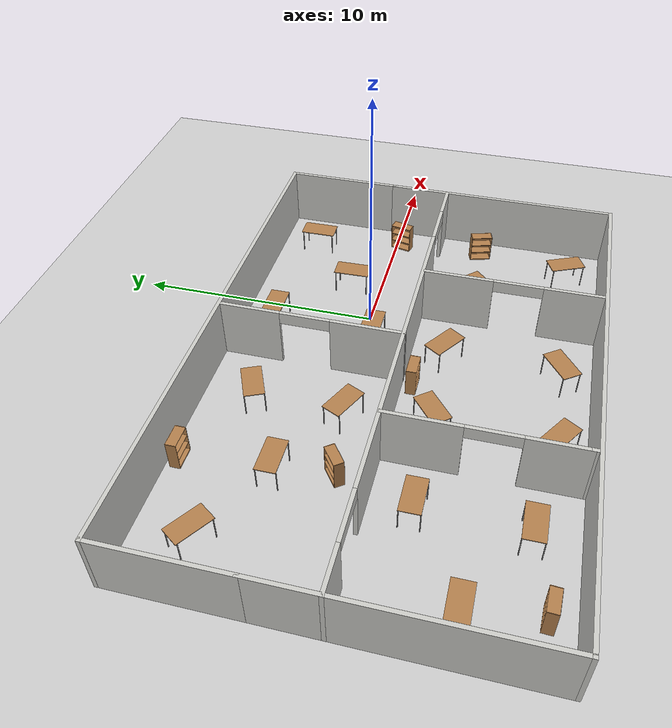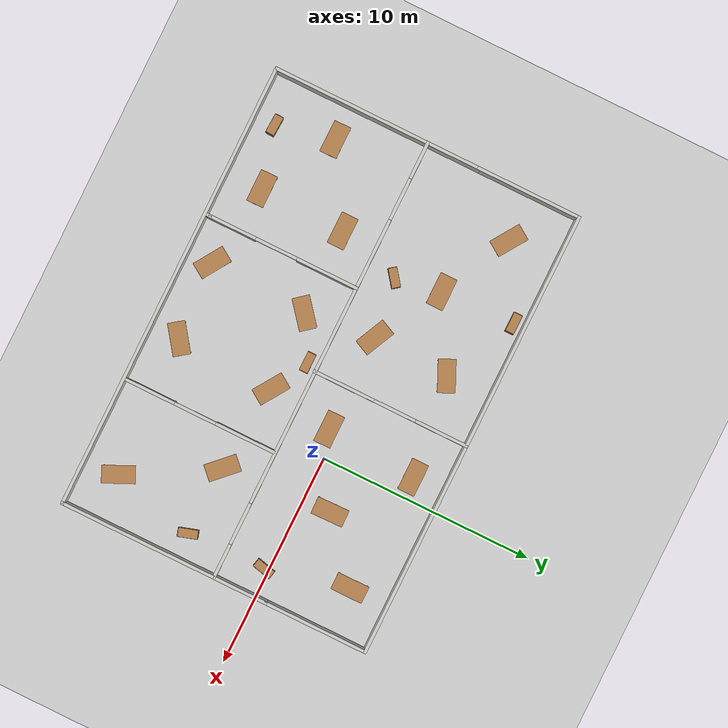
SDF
<sdf version="1.6">
 <world name="default">
  <light name="sun" type="directional">
   <pose>0 0 10 0 -0 0</pose>
   <diffuse>0.8 0.8 0.8 1</diffuse>
   <specular>0.2 0.2 0.2 1</specular>
   <attenuation>
    <range>1000</range>
    <constant>0.9</constant>
    <linear>0.01</linear>
    <quadratic>0.001</quadratic>
   </attenuation>
   <direction>-0.5 0.1 -0.9</direction>
  </light>
  <model name="ground_plane">
   <static>1</static>
   <link name="link">
    <collision name="collision">
     <geometry><plane><normal>0 0 1</normal><size>100 100</size></plane></geometry>
     <surface>
      <contact><collide_bitmask>65535</collide_bitmask></contact>
      <friction><ode><mu>100</mu><mu2>50</mu2></ode></friction>
     </surface>
    </collision>
    <visual name="visual">
     <cast_shadows>0</cast_shadows>
     <geometry><plane><normal>0 0 1</normal><size>100 100</size></plane></geometry>
     <material>
      <script><uri>file://media/materials/scripts/gazebo.material</uri><name>Gazebo/Grey</name></script>
     </material>
    </visual>
   </link>
  </model>
  <gravity>0 0 -9.8</gravity>
  <magnetic_field>6e-06 2.3e-05 -4.2e-05</magnetic_field>
  <atmosphere type="adiabatic"/>
  <physics name="default_physics" default="0" type="ode">
   <max_step_size>0.001</max_step_size>
   <real_time_factor>1</real_time_factor>
   <real_time_update_rate>1000</real_time_update_rate>
  </physics>
  <scene><ambient>0.4 0.4 0.4 1</ambient><background>0.7 0.7 0.7 1</background><shadows>1</shadows></scene>
  <spherical_coordinates>
   <surface_model>EARTH_WGS84</surface_model>
   <latitude_deg>0</latitude_deg>
   <longitude_deg>0</longitude_deg>
   <elevation>0</elevation>
   <heading_deg>0</heading_deg>
  </spherical_coordinates>
  <model name="myworld">
   <pose>-3.80352 -2.02959 0 0 -0 0</pose>
   <link name="Wall_0">
    <collision name="Wall_0_Collision">
     <geometry><box><size>10 0.15 2.5</size></box></geometry>
     <pose>0 0 1.25 0 -0 0</pose>
    </collision>
    <visual name="Wall_0_Visual">
     <pose>0 0 1.25 0 -0 0</pose>
     <geometry><box><size>10 0.15 2.5</size></box></geometry>
     <material>
      <script><uri>file://media/materials/scripts/gazebo.material</uri><name>Gazebo/CeilingTiled</name></script>
      <ambient>1 1 0 1</ambient>
     </material>
     <meta><layer>0</layer></meta>
    </visual>
    <pose>-10.5499 -2.425 0 0 0 -1.5708</pose>
   </link>
   <link name="Wall_1">
    <collision name="Wall_1_Collision">
     <geometry><box><size>21.25 0.15 2.5</size></box></geometry>
     <pose>0 0 1.25 0 -0 0</pose>
    </collision>
    <visual name="Wall_1_Visual">
     <pose>0 0 1.25 0 -0 0</pose>
     <geometry><box><size>21.25 0.15 2.5</size></box></geometry>
     <material>
      <script><uri>file://media/materials/scripts/gazebo.material</uri><name>Gazebo/CeilingTiled</name></script>
      <ambient>0.333333 1 0 1</ambient>
     </material>
     <meta><layer>0</layer></meta>
    </visual>
    <pose>6.1e-05 -7.35 0 0 -0 0</pose>
   </link>
   <link name="Wall_16">
    <pose>-6.2e-05 0.001581 0 0 -0 0</pose>
    <visual name="Wall_16_Visual_0">
     <pose>-9.72617 0 1.25 0 -0 0</pose>
     <geometry><box><size>1.79767 0.15 2.5</size></box></geometry>
     <material>
      <script><uri>file://media/materials/scripts/gazebo.material</uri><name>Gazebo/CeilingTiled</name></script>
      <ambient>0 0 0 1</ambient>
     </material>
     <meta><layer>0</layer></meta>
    </visual>
    <collision name="Wall_16_Collision_0">
     <geometry><box><size>1.79767 0.15 2.5</size></box></geometry>
     <pose>-9.72617 0 1.25 0 -0 0</pose>
    </collision>
    <visual name="Wall_16_Visual_1">
     <pose>0.056227 0 1.25 0 -0 0</pose>
     <geometry><box><size>13.7671 0.15 2.5</size></box></geometry>
     <material>
      <script><uri>file://media/materials/scripts/gazebo.material</uri><name>Gazebo/CeilingTiled</name></script>
      <ambient>0 0 0 1</ambient>
     </material>
     <meta><layer>0</layer></meta>
    </visual>
    <collision name="Wall_16_Collision_1">
     <geometry><box><size>13.7671 0.15 2.5</size></box></geometry>
     <pose>0.056227 0 1.25 0 -0 0</pose>
    </collision>
    <visual name="Wall_16_Visual_2">
     <pose>9.78239 0 1.25 0 -0 0</pose>
     <geometry><box><size>1.68521 0.15 2.5</size></box></geometry>
     <material>
      <script><uri>file://media/materials/scripts/gazebo.material</uri><name>Gazebo/CeilingTiled</name></script>
      <ambient>0 0 0 1</ambient>
     </material>
     <meta><layer>0</layer></meta>
    </visual>
    <collision name="Wall_16_Collision_2">
     <geometry><box><size>1.68521 0.15 2.5</size></box></geometry>
     <pose>9.78239 0 1.25 0 -0 0</pose>
    </collision>
    <visual name="Wall_16_Visual_3">
     <pose>-7.82733 0 2.25 0 -0 0</pose>
     <geometry><box><size>2 0.15 0.5</size></box></geometry>
     <material>
      <script><uri>file://media/materials/scripts/gazebo.material</uri><name>Gazebo/CeilingTiled</name></script>
      <ambient>0 0 0 1</ambient>
     </material>
     <meta><layer>0</layer></meta>
    </visual>
    <collision name="Wall_16_Collision_3">
     <geometry><box><size>2 0.15 0.5</size></box></geometry>
     <pose>-7.82733 0 2.25 0 -0 0</pose>
    </collision>
    <visual name="Wall_16_Visual_4">
     <pose>7.93979 0 2.25 0 -0 0</pose>
     <geometry><box><size>2 0.15 0.5</size></box></geometry>
     <material>
      <script><uri>file://media/materials/scripts/gazebo.material</uri><name>Gazebo/CeilingTiled</name></script>
      <ambient>0 0 0 1</ambient>
     </material>
     <meta><layer>0</layer></meta>
    </visual>
    <collision name="Wall_16_Collision_4">
     <geometry><box><size>2 0.15 0.5</size></box></geometry>
     <pose>7.93979 0 2.25 0 -0 0</pose>
    </collision>
   </link>
   <link name="Wall_2">
    <collision name="Wall_2_Collision">
     <geometry><box><size>10 0.15 2.5</size></box></geometry>
     <pose>0 0 1.25 0 -0 0</pose>
    </collision>
    <visual name="Wall_2_Visual">
     <pose>0 0 1.25 0 -0 0</pose>
     <geometry><box><size>10 0.15 2.5</size></box></geometry>
     <material>
      <script><uri>file://media/materials/scripts/gazebo.material</uri><name>Gazebo/CeilingTiled</name></script>
      <ambient>0.333333 0.333333 1 1</ambient>
     </material>
     <meta><layer>0</layer></meta>
    </visual>
    <pose>10.5501 -2.425 0 0 -0 1.5708</pose>
   </link>
   <link name="Wall_25">
    <pose>-3.5035 -3.55368 0 0 0 -1.5708</pose>
    <visual name="Wall_25_Visual_0">
     <pose>-2.14633 0 1.25 0 -0 0</pose>
     <geometry><box><size>2.95734 0.15 2.5</size></box></geometry>
     <material>
      <script><uri>file://media/materials/scripts/gazebo.material</uri><name>Gazebo/CeilingTiled</name></script>
      <ambient>0.333333 0 0 1</ambient>
     </material>
     <meta><layer>0</layer></meta>
    </visual>
    <collision name="Wall_25_Collision_0">
     <geometry><box><size>2.95734 0.15 2.5</size></box></geometry>
     <pose>-2.14633 0 1.25 0 -0 0</pose>
    </collision>
    <visual name="Wall_25_Visual_1">
     <pose>2.47867 0 1.25 0 -0 0</pose>
     <geometry><box><size>2.29266 0.15 2.5</size></box></geometry>
     <material>
      <script><uri>file://media/materials/scripts/gazebo.material</uri><name>Gazebo/CeilingTiled</name></script>
      <ambient>0.333333 0 0 1</ambient>
     </material>
     <meta><layer>0</layer></meta>
    </visual>
    <collision name="Wall_25_Collision_1">
     <geometry><box><size>2.29266 0.15 2.5</size></box></geometry>
     <pose>2.47867 0 1.25 0 -0 0</pose>
    </collision>
    <visual name="Wall_25_Visual_2">
     <pose>0.332335 0 2.25 0 -0 0</pose>
     <geometry><box><size>2 0.15 0.5</size></box></geometry>
     <material>
      <script><uri>file://media/materials/scripts/gazebo.material</uri><name>Gazebo/CeilingTiled</name></script>
      <ambient>0.333333 0 0 1</ambient>
     </material>
     <meta><layer>0</layer></meta>
    </visual>
    <collision name="Wall_25_Collision_2">
     <geometry><box><size>2 0.15 0.5</size></box></geometry>
     <pose>0.332335 0 2.25 0 -0 0</pose>
    </collision>
   </link>
   <link name="Wall_27">
    <pose>4.49862 -3.64673 0 0 0 -1.5708</pose>
    <visual name="Wall_27_Visual_0">
     <pose>-2.19286 0 1.25 0 -0 0</pose>
     <geometry><box><size>2.86429 0.15 2.5</size></box></geometry>
     <material>
      <script><uri>file://media/materials/scripts/gazebo.material</uri><name>Gazebo/CeilingTiled</name></script>
      <ambient>0.666667 0 0.498039 1</ambient>
     </material>
     <meta><layer>0</layer></meta>
    </visual>
    <collision name="Wall_27_Collision_0">
     <geometry><box><size>2.86429 0.15 2.5</size></box></geometry>
     <pose>-2.19286 0 1.25 0 -0 0</pose>
    </collision>
    <visual name="Wall_27_Visual_1">
     <pose>2.43214 0 1.25 0 -0 0</pose>
     <geometry><box><size>2.38571 0.15 2.5</size></box></geometry>
     <material>
      <script><uri>file://media/materials/scripts/gazebo.material</uri><name>Gazebo/CeilingTiled</name></script>
      <ambient>0.666667 0 0.498039 1</ambient>
     </material>
     <meta><layer>0</layer></meta>
    </visual>
    <collision name="Wall_27_Collision_1">
     <geometry><box><size>2.38571 0.15 2.5</size></box></geometry>
     <pose>2.43214 0 1.25 0 -0 0</pose>
    </collision>
    <visual name="Wall_27_Visual_2">
     <pose>0.239287 0 2.25 0 -0 0</pose>
     <geometry><box><size>2 0.15 0.5</size></box></geometry>
     <material>
      <script><uri>file://media/materials/scripts/gazebo.material</uri><name>Gazebo/CeilingTiled</name></script>
      <ambient>0.666667 0 0.498039 1</ambient>
     </material>
     <meta><layer>0</layer></meta>
    </visual>
    <collision name="Wall_27_Collision_2">
     <geometry><box><size>2 0.15 0.5</size></box></geometry>
     <pose>0.239287 0 2.25 0 -0 0</pose>
    </collision>
   </link>
   <link name="Wall_34">
    <pose>0.552412 3.6586 0 0 -0 1.5708</pose>
    <visual name="Wall_34_Visual_0">
     <pose>-2.27068 0 1.25 0 -0 0</pose>
     <geometry><box><size>2.95863 0.15 2.5</size></box></geometry>
     <material>
      <script><uri>file://media/materials/scripts/gazebo.material</uri><name>Gazebo/CeilingTiled</name></script>
      <ambient>0 0.666667 0.498039 1</ambient>
     </material>
     <meta><layer>0</layer></meta>
    </visual>
    <collision name="Wall_34_Collision_0">
     <geometry><box><size>2.95863 0.15 2.5</size></box></geometry>
     <pose>-2.27068 0 1.25 0 -0 0</pose>
    </collision>
    <visual name="Wall_34_Visual_1">
     <pose>2.47932 0 1.25 0 -0 0</pose>
     <geometry><box><size>2.54137 0.15 2.5</size></box></geometry>
     <material>
      <script><uri>file://media/materials/scripts/gazebo.material</uri><name>Gazebo/CeilingTiled</name></script>
      <ambient>0 0.666667 0.498039 1</ambient>
     </material>
     <meta><layer>0</layer></meta>
    </visual>
    <collision name="Wall_34_Collision_1">
     <geometry><box><size>2.54137 0.15 2.5</size></box></geometry>
     <pose>2.47932 0 1.25 0 -0 0</pose>
    </collision>
    <visual name="Wall_34_Visual_2">
     <pose>0.208629 0 2.25 0 -0 0</pose>
     <geometry><box><size>2 0.15 0.5</size></box></geometry>
     <material>
      <script><uri>file://media/materials/scripts/gazebo.material</uri><name>Gazebo/CeilingTiled</name></script>
      <ambient>0 0.666667 0.498039 1</ambient>
     </material>
     <meta><layer>0</layer></meta>
    </visual>
    <collision name="Wall_34_Collision_2">
     <geometry><box><size>2 0.15 0.5</size></box></geometry>
     <pose>0.208629 0 2.25 0 -0 0</pose>
    </collision>
   </link>
   <link name="Wall_36">
    <collision name="Wall_36_Collision">
     <geometry><box><size>0.25 0.15 2.5</size></box></geometry>
     <pose>0 0 1.25 0 -0 0</pose>
    </collision>
    <visual name="Wall_36_Visual">
     <pose>0 0 1.25 0 -0 0</pose>
     <geometry><box><size>0.25 0.15 2.5</size></box></geometry>
     <material>
      <script><uri>file://media/materials/scripts/gazebo.material</uri><name>Gazebo/CeilingTiled</name></script>
      <ambient>1 1 1 1</ambient>
     </material>
     <meta><layer>0</layer></meta>
    </visual>
    <pose>-3.5035 -7.15368 0 0 0 -1.5708</pose>
   </link>
   <link name="Wall_5">
    <collision name="Wall_5_Collision">
     <geometry><box><size>5 0.15 2.5</size></box></geometry>
     <pose>0 0 1.25 0 -0 0</pose>
    </collision>
    <visual name="Wall_5_Visual">
     <pose>0 0 1.25 0 -0 0</pose>
     <geometry><box><size>5 0.15 2.5</size></box></geometry>
     <material>
      <script><uri>file://media/materials/scripts/gazebo.material</uri><name>Gazebo/CeilingTiled</name></script>
      <ambient>1 1 0 1</ambient>
     </material>
     <meta><layer>0</layer></meta>
    </visual>
    <pose>-10.5499 4.925 0 0 -0 1.5708</pose>
   </link>
   <link name="Wall_6">
    <collision name="Wall_6_Collision">
     <geometry><box><size>21.25 0.15 2.5</size></box></geometry>
     <pose>0 0 1.25 0 -0 0</pose>
    </collision>
    <visual name="Wall_6_Visual">
     <pose>0 0 1.25 0 -0 0</pose>
     <geometry><box><size>21.25 0.15 2.5</size></box></geometry>
     <material>
      <script><uri>file://media/materials/scripts/gazebo.material</uri><name>Gazebo/CeilingTiled</name></script>
      <ambient>1 0 0 1</ambient>
     </material>
     <meta><layer>0</layer></meta>
    </visual>
    <pose>6.1e-05 7.35 0 0 -0 0</pose>
   </link>
   <link name="Wall_7">
    <collision name="Wall_7_Collision">
     <geometry><box><size>5 0.15 2.5</size></box></geometry>
     <pose>0 0 1.25 0 -0 0</pose>
    </collision>
    <visual name="Wall_7_Visual">
     <pose>0 0 1.25 0 -0 0</pose>
     <geometry><box><size>5 0.15 2.5</size></box></geometry>
     <material>
      <script><uri>file://media/materials/scripts/gazebo.material</uri><name>Gazebo/CeilingTiled</name></script>
      <ambient>0.333333 0.333333 1 1</ambient>
     </material>
     <meta><layer>0</layer></meta>
    </visual>
    <pose>10.5501 4.925 0 0 0 -1.5708</pose>
   </link>
   <static>1</static>
  </model>
  <model name="table">
   <static>1</static>
   <link name="link">
    <collision name="surface">
     <pose>0 0 1 0 -0 0</pose>
     <geometry><box><size>1.5 0.8 0.03</size></box></geometry>
     <surface><friction><ode><mu>0.6</mu><mu2>0.6</mu2></ode></friction></surface>
    </collision>
    <visual name="visual1">
     <pose>0 0 1 0 -0 0</pose>
     <geometry><box><size>1.5 0.8 0.03</size></box></geometry>
     <material>
      <script><uri>file://media/materials/scripts/gazebo.material</uri><name>Gazebo/Wood</name></script>
     </material>
    </visual>
    <collision name="front_left_leg">
     <pose>0.68 0.38 0.5 0 -0 0</pose>
     <geometry><cylinder><radius>0.02</radius><length>1</length></cylinder></geometry>
    </collision>
    <visual name="front_left_leg">
     <pose>0.68 0.38 0.5 0 -0 0</pose>
     <geometry><cylinder><radius>0.02</radius><length>1</length></cylinder></geometry>
     <material>
      <script><uri>file://media/materials/scripts/gazebo.material</uri><name>Gazebo/Grey</name></script>
     </material>
    </visual>
    <collision name="front_right_leg">
     <pose>0.68 -0.38 0.5 0 -0 0</pose>
     <geometry><cylinder><radius>0.02</radius><length>1</length></cylinder></geometry>
    </collision>
    <visual name="front_right_leg">
     <pose>0.68 -0.38 0.5 0 -0 0</pose>
     <geometry><cylinder><radius>0.02</radius><length>1</length></cylinder></geometry>
     <material>
      <script><uri>file://media/materials/scripts/gazebo.material</uri><name>Gazebo/Grey</name></script>
     </material>
    </visual>
    <collision name="back_right_leg">
     <pose>-0.68 -0.38 0.5 0 -0 0</pose>
     <geometry><cylinder><radius>0.02</radius><length>1</length></cylinder></geometry>
    </collision>
    <visual name="back_right_leg">
     <pose>-0.68 -0.38 0.5 0 -0 0</pose>
     <geometry><cylinder><radius>0.02</radius><length>1</length></cylinder></geometry>
     <material>
      <script><uri>file://media/materials/scripts/gazebo.material</uri><name>Gazebo/Grey</name></script>
     </material>
    </visual>
    <collision name="back_left_leg">
     <pose>-0.68 0.38 0.5 0 -0 0</pose>
     <geometry><cylinder><radius>0.02</radius><length>1</length></cylinder></geometry>
    </collision>
    <visual name="back_left_leg">
     <pose>-0.68 0.38 0.5 0 -0 0</pose>
     <geometry><cylinder><radius>0.02</radius><length>1</length></cylinder></geometry>
     <material>
      <script><uri>file://media/materials/scripts/gazebo.material</uri><name>Gazebo/Grey</name></script>
     </material>
    </visual>
   </link>
   <pose>-5.759 -0.343504 0 0 0 -0.441227</pose>
  </model>
  <model name="table_0">
   <static>1</static>
   <link name="link">
    <collision name="surface">
     <pose>0 0 1 0 -0 0</pose>
     <geometry><box><size>1.5 0.8 0.03</size></box></geometry>
     <surface><friction><ode><mu>0.6</mu><mu2>0.6</mu2></ode></friction></surface>
    </collision>
    <visual name="visual1">
     <pose>0 0 1 0 -0 0</pose>
     <geometry><box><size>1.5 0.8 0.03</size></box></geometry>
     <material>
      <script><uri>file://media/materials/scripts/gazebo.material</uri><name>Gazebo/Wood</name></script>
     </material>
    </visual>
    <collision name="front_left_leg">
     <pose>0.68 0.38 0.5 0 -0 0</pose>
     <geometry><cylinder><radius>0.02</radius><length>1</length></cylinder></geometry>
    </collision>
    <visual name="front_left_leg">
     <pose>0.68 0.38 0.5 0 -0 0</pose>
     <geometry><cylinder><radius>0.02</radius><length>1</length></cylinder></geometry>
     <material>
      <script><uri>file://media/materials/scripts/gazebo.material</uri><name>Gazebo/Grey</name></script>
     </material>
    </visual>
    <collision name="front_right_leg">
     <pose>0.68 -0.38 0.5 0 -0 0</pose>
     <geometry><cylinder><radius>0.02</radius><length>1</length></cylinder></geometry>
    </collision>
    <visual name="front_right_leg">
     <pose>0.68 -0.38 0.5 0 -0 0</pose>
     <geometry><cylinder><radius>0.02</radius><length>1</length></cylinder></geometry>
     <material>
      <script><uri>file://media/materials/scripts/gazebo.material</uri><name>Gazebo/Grey</name></script>
     </material>
    </visual>
    <collision name="back_right_leg">
     <pose>-0.68 -0.38 0.5 0 -0 0</pose>
     <geometry><cylinder><radius>0.02</radius><length>1</length></cylinder></geometry>
    </collision>
    <visual name="back_right_leg">
     <pose>-0.68 -0.38 0.5 0 -0 0</pose>
     <geometry><cylinder><radius>0.02</radius><length>1</length></cylinder></geometry>
     <material>
      <script><uri>file://media/materials/scripts/gazebo.material</uri><name>Gazebo/Grey</name></script>
     </material>
    </visual>
    <collision name="back_left_leg">
     <pose>-0.68 0.38 0.5 0 -0 0</pose>
     <geometry><cylinder><radius>0.02</radius><length>1</length></cylinder></geometry>
    </collision>
    <visual name="back_left_leg">
     <pose>-0.68 0.38 0.5 0 -0 0</pose>
     <geometry><cylinder><radius>0.02</radius><length>1</length></cylinder></geometry>
     <material>
      <script><uri>file://media/materials/scripts/gazebo.material</uri><name>Gazebo/Grey</name></script>
     </material>
    </visual>
   </link>
   <pose>-5.63329 3.22435 0 0 -0 0.426782</pose>
  </model>
  <model name="table_1">
   <static>1</static>
   <link name="link">
    <collision name="surface">
     <pose>0 0 1 0 -0 0</pose>
     <geometry><box><size>1.5 0.8 0.03</size></box></geometry>
     <surface><friction><ode><mu>0.6</mu><mu2>0.6</mu2></ode></friction></surface>
    </collision>
    <visual name="visual1">
     <pose>0 0 1 0 -0 0</pose>
     <geometry><box><size>1.5 0.8 0.03</size></box></geometry>
     <material>
      <script><uri>file://media/materials/scripts/gazebo.material</uri><name>Gazebo/Wood</name></script>
     </material>
    </visual>
    <collision name="front_left_leg">
     <pose>0.68 0.38 0.5 0 -0 0</pose>
     <geometry><cylinder><radius>0.02</radius><length>1</length></cylinder></geometry>
    </collision>
    <visual name="front_left_leg">
     <pose>0.68 0.38 0.5 0 -0 0</pose>
     <geometry><cylinder><radius>0.02</radius><length>1</length></cylinder></geometry>
     <material>
      <script><uri>file://media/materials/scripts/gazebo.material</uri><name>Gazebo/Grey</name></script>
     </material>
    </visual>
    <collision name="front_right_leg">
     <pose>0.68 -0.38 0.5 0 -0 0</pose>
     <geometry><cylinder><radius>0.02</radius><length>1</length></cylinder></geometry>
    </collision>
    <visual name="front_right_leg">
     <pose>0.68 -0.38 0.5 0 -0 0</pose>
     <geometry><cylinder><radius>0.02</radius><length>1</length></cylinder></geometry>
     <material>
      <script><uri>file://media/materials/scripts/gazebo.material</uri><name>Gazebo/Grey</name></script>
     </material>
    </visual>
    <collision name="back_right_leg">
     <pose>-0.68 -0.38 0.5 0 -0 0</pose>
     <geometry><cylinder><radius>0.02</radius><length>1</length></cylinder></geometry>
    </collision>
    <visual name="back_right_leg">
     <pose>-0.68 -0.38 0.5 0 -0 0</pose>
     <geometry><cylinder><radius>0.02</radius><length>1</length></cylinder></geometry>
     <material>
      <script><uri>file://media/materials/scripts/gazebo.material</uri><name>Gazebo/Grey</name></script>
     </material>
    </visual>
    <collision name="back_left_leg">
     <pose>-0.68 0.38 0.5 0 -0 0</pose>
     <geometry><cylinder><radius>0.02</radius><length>1</length></cylinder></geometry>
    </collision>
    <visual name="back_left_leg">
     <pose>-0.68 0.38 0.5 0 -0 0</pose>
     <geometry><cylinder><radius>0.02</radius><length>1</length></cylinder></geometry>
     <material>
      <script><uri>file://media/materials/scripts/gazebo.material</uri><name>Gazebo/Grey</name></script>
     </material>
    </visual>
   </link>
   <pose>-8.85797 1.39413 0 0 -0 0</pose>
  </model>
  <model name="table_2">
   <static>1</static>
   <link name="link">
    <collision name="surface">
     <pose>0 0 1 0 -0 0</pose>
     <geometry><box><size>1.5 0.8 0.03</size></box></geometry>
     <surface><friction><ode><mu>0.6</mu><mu2>0.6</mu2></ode></friction></surface>
    </collision>
    <visual name="visual1">
     <pose>0 0 1 0 -0 0</pose>
     <geometry><box><size>1.5 0.8 0.03</size></box></geometry>
     <material>
      <script><uri>file://media/materials/scripts/gazebo.material</uri><name>Gazebo/Wood</name></script>
     </material>
    </visual>
    <collision name="front_left_leg">
     <pose>0.68 0.38 0.5 0 -0 0</pose>
     <geometry><cylinder><radius>0.02</radius><length>1</length></cylinder></geometry>
    </collision>
    <visual name="front_left_leg">
     <pose>0.68 0.38 0.5 0 -0 0</pose>
     <geometry><cylinder><radius>0.02</radius><length>1</length></cylinder></geometry>
     <material>
      <script><uri>file://media/materials/scripts/gazebo.material</uri><name>Gazebo/Grey</name></script>
     </material>
    </visual>
    <collision name="front_right_leg">
     <pose>0.68 -0.38 0.5 0 -0 0</pose>
     <geometry><cylinder><radius>0.02</radius><length>1</length></cylinder></geometry>
    </collision>
    <visual name="front_right_leg">
     <pose>0.68 -0.38 0.5 0 -0 0</pose>
     <geometry><cylinder><radius>0.02</radius><length>1</length></cylinder></geometry>
     <material>
      <script><uri>file://media/materials/scripts/gazebo.material</uri><name>Gazebo/Grey</name></script>
     </material>
    </visual>
    <collision name="back_right_leg">
     <pose>-0.68 -0.38 0.5 0 -0 0</pose>
     <geometry><cylinder><radius>0.02</radius><length>1</length></cylinder></geometry>
    </collision>
    <visual name="back_right_leg">
     <pose>-0.68 -0.38 0.5 0 -0 0</pose>
     <geometry><cylinder><radius>0.02</radius><length>1</length></cylinder></geometry>
     <material>
      <script><uri>file://media/materials/scripts/gazebo.material</uri><name>Gazebo/Grey</name></script>
     </material>
    </visual>
    <collision name="back_left_leg">
     <pose>-0.68 0.38 0.5 0 -0 0</pose>
     <geometry><cylinder><radius>0.02</radius><length>1</length></cylinder></geometry>
    </collision>
    <visual name="back_left_leg">
     <pose>-0.68 0.38 0.5 0 -0 0</pose>
     <geometry><cylinder><radius>0.02</radius><length>1</length></cylinder></geometry>
     <material>
      <script><uri>file://media/materials/scripts/gazebo.material</uri><name>Gazebo/Grey</name></script>
     </material>
    </visual>
   </link>
   <pose>-12.1705 3.04957 0 0 0 -0.585762</pose>
  </model>
  <model name="table_3">
   <static>1</static>
   <link name="link">
    <collision name="surface">
     <pose>0 0 1 0 -0 0</pose>
     <geometry><box><size>1.5 0.8 0.03</size></box></geometry>
     <surface><friction><ode><mu>0.6</mu><mu2>0.6</mu2></ode></friction></surface>
    </collision>
    <visual name="visual1">
     <pose>0 0 1 0 -0 0</pose>
     <geometry><box><size>1.5 0.8 0.03</size></box></geometry>
     <material>
      <script><uri>file://media/materials/scripts/gazebo.material</uri><name>Gazebo/Wood</name></script>
     </material>
    </visual>
    <collision name="front_left_leg">
     <pose>0.68 0.38 0.5 0 -0 0</pose>
     <geometry><cylinder><radius>0.02</radius><length>1</length></cylinder></geometry>
    </collision>
    <visual name="front_left_leg">
     <pose>0.68 0.38 0.5 0 -0 0</pose>
     <geometry><cylinder><radius>0.02</radius><length>1</length></cylinder></geometry>
     <material>
      <script><uri>file://media/materials/scripts/gazebo.material</uri><name>Gazebo/Grey</name></script>
     </material>
    </visual>
    <collision name="front_right_leg">
     <pose>0.68 -0.38 0.5 0 -0 0</pose>
     <geometry><cylinder><radius>0.02</radius><length>1</length></cylinder></geometry>
    </collision>
    <visual name="front_right_leg">
     <pose>0.68 -0.38 0.5 0 -0 0</pose>
     <geometry><cylinder><radius>0.02</radius><length>1</length></cylinder></geometry>
     <material>
      <script><uri>file://media/materials/scripts/gazebo.material</uri><name>Gazebo/Grey</name></script>
     </material>
    </visual>
    <collision name="back_right_leg">
     <pose>-0.68 -0.38 0.5 0 -0 0</pose>
     <geometry><cylinder><radius>0.02</radius><length>1</length></cylinder></geometry>
    </collision>
    <visual name="back_right_leg">
     <pose>-0.68 -0.38 0.5 0 -0 0</pose>
     <geometry><cylinder><radius>0.02</radius><length>1</length></cylinder></geometry>
     <material>
      <script><uri>file://media/materials/scripts/gazebo.material</uri><name>Gazebo/Grey</name></script>
     </material>
    </visual>
    <collision name="back_left_leg">
     <pose>-0.68 0.38 0.5 0 -0 0</pose>
     <geometry><cylinder><radius>0.02</radius><length>1</length></cylinder></geometry>
    </collision>
    <visual name="back_left_leg">
     <pose>-0.68 0.38 0.5 0 -0 0</pose>
     <geometry><cylinder><radius>0.02</radius><length>1</length></cylinder></geometry>
     <material>
      <script><uri>file://media/materials/scripts/gazebo.material</uri><name>Gazebo/Grey</name></script>
     </material>
    </visual>
   </link>
   <pose>4.58009 3.52405 0 0 0 -1.56695</pose>
  </model>
  <model name="table_4">
   <static>1</static>
   <link name="link">
    <collision name="surface">
     <pose>0 0 1 0 -0 0</pose>
     <geometry><box><size>1.5 0.8 0.03</size></box></geometry>
     <surface><friction><ode><mu>0.6</mu><mu2>0.6</mu2></ode></friction></surface>
    </collision>
    <visual name="visual1">
     <pose>0 0 1 0 -0 0</pose>
     <geometry><box><size>1.5 0.8 0.03</size></box></geometry>
     <material>
      <script><uri>file://media/materials/scripts/gazebo.material</uri><name>Gazebo/Wood</name></script>
     </material>
    </visual>
    <collision name="front_left_leg">
     <pose>0.68 0.38 0.5 0 -0 0</pose>
     <geometry><cylinder><radius>0.02</radius><length>1</length></cylinder></geometry>
    </collision>
    <visual name="front_left_leg">
     <pose>0.68 0.38 0.5 0 -0 0</pose>
     <geometry><cylinder><radius>0.02</radius><length>1</length></cylinder></geometry>
     <material>
      <script><uri>file://media/materials/scripts/gazebo.material</uri><name>Gazebo/Grey</name></script>
     </material>
    </visual>
    <collision name="front_right_leg">
     <pose>0.68 -0.38 0.5 0 -0 0</pose>
     <geometry><cylinder><radius>0.02</radius><length>1</length></cylinder></geometry>
    </collision>
    <visual name="front_right_leg">
     <pose>0.68 -0.38 0.5 0 -0 0</pose>
     <geometry><cylinder><radius>0.02</radius><length>1</length></cylinder></geometry>
     <material>
      <script><uri>file://media/materials/scripts/gazebo.material</uri><name>Gazebo/Grey</name></script>
     </material>
    </visual>
    <collision name="back_right_leg">
     <pose>-0.68 -0.38 0.5 0 -0 0</pose>
     <geometry><cylinder><radius>0.02</radius><length>1</length></cylinder></geometry>
    </collision>
    <visual name="back_right_leg">
     <pose>-0.68 -0.38 0.5 0 -0 0</pose>
     <geometry><cylinder><radius>0.02</radius><length>1</length></cylinder></geometry>
     <material>
      <script><uri>file://media/materials/scripts/gazebo.material</uri><name>Gazebo/Grey</name></script>
     </material>
    </visual>
    <collision name="back_left_leg">
     <pose>-0.68 0.38 0.5 0 -0 0</pose>
     <geometry><cylinder><radius>0.02</radius><length>1</length></cylinder></geometry>
    </collision>
    <visual name="back_left_leg">
     <pose>-0.68 0.38 0.5 0 -0 0</pose>
     <geometry><cylinder><radius>0.02</radius><length>1</length></cylinder></geometry>
     <material>
      <script><uri>file://media/materials/scripts/gazebo.material</uri><name>Gazebo/Grey</name></script>
     </material>
    </visual>
   </link>
   <pose>1.974 1.27026 0 0 0 -1.54787</pose>
  </model>
  <model name="table_5">
   <static>1</static>
   <link name="link">
    <collision name="surface">
     <pose>0 0 1 0 -0 0</pose>
     <geometry><box><size>1.5 0.8 0.03</size></box></geometry>
     <surface><friction><ode><mu>0.6</mu><mu2>0.6</mu2></ode></friction></surface>
    </collision>
    <visual name="visual1">
     <pose>0 0 1 0 -0 0</pose>
     <geometry><box><size>1.5 0.8 0.03</size></box></geometry>
     <material>
      <script><uri>file://media/materials/scripts/gazebo.material</uri><name>Gazebo/Wood</name></script>
     </material>
    </visual>
    <collision name="front_left_leg">
     <pose>0.68 0.38 0.5 0 -0 0</pose>
     <geometry><cylinder><radius>0.02</radius><length>1</length></cylinder></geometry>
    </collision>
    <visual name="front_left_leg">
     <pose>0.68 0.38 0.5 0 -0 0</pose>
     <geometry><cylinder><radius>0.02</radius><length>1</length></cylinder></geometry>
     <material>
      <script><uri>file://media/materials/scripts/gazebo.material</uri><name>Gazebo/Grey</name></script>
     </material>
    </visual>
    <collision name="front_right_leg">
     <pose>0.68 -0.38 0.5 0 -0 0</pose>
     <geometry><cylinder><radius>0.02</radius><length>1</length></cylinder></geometry>
    </collision>
    <visual name="front_right_leg">
     <pose>0.68 -0.38 0.5 0 -0 0</pose>
     <geometry><cylinder><radius>0.02</radius><length>1</length></cylinder></geometry>
     <material>
      <script><uri>file://media/materials/scripts/gazebo.material</uri><name>Gazebo/Grey</name></script>
     </material>
    </visual>
    <collision name="back_right_leg">
     <pose>-0.68 -0.38 0.5 0 -0 0</pose>
     <geometry><cylinder><radius>0.02</radius><length>1</length></cylinder></geometry>
    </collision>
    <visual name="back_right_leg">
     <pose>-0.68 -0.38 0.5 0 -0 0</pose>
     <geometry><cylinder><radius>0.02</radius><length>1</length></cylinder></geometry>
     <material>
      <script><uri>file://media/materials/scripts/gazebo.material</uri><name>Gazebo/Grey</name></script>
     </material>
    </visual>
    <collision name="back_left_leg">
     <pose>-0.68 0.38 0.5 0 -0 0</pose>
     <geometry><cylinder><radius>0.02</radius><length>1</length></cylinder></geometry>
    </collision>
    <visual name="back_left_leg">
     <pose>-0.68 0.38 0.5 0 -0 0</pose>
     <geometry><cylinder><radius>0.02</radius><length>1</length></cylinder></geometry>
     <material>
      <script><uri>file://media/materials/scripts/gazebo.material</uri><name>Gazebo/Grey</name></script>
     </material>
    </visual>
   </link>
   <pose>-1.27098 -0.368858 0 0 -0 0</pose>
  </model>
  <model name="table_6">
   <static>1</static>
   <link name="link">
    <collision name="surface">
     <pose>0 0 1 0 -0 0</pose>
     <geometry><box><size>1.5 0.8 0.03</size></box></geometry>
     <surface><friction><ode><mu>0.6</mu><mu2>0.6</mu2></ode></friction></surface>
    </collision>
    <visual name="visual1">
     <pose>0 0 1 0 -0 0</pose>
     <geometry><box><size>1.5 0.8 0.03</size></box></geometry>
     <material>
      <script><uri>file://media/materials/scripts/gazebo.material</uri><name>Gazebo/Wood</name></script>
     </material>
    </visual>
    <collision name="front_left_leg">
     <pose>0.68 0.38 0.5 0 -0 0</pose>
     <geometry><cylinder><radius>0.02</radius><length>1</length></cylinder></geometry>
    </collision>
    <visual name="front_left_leg">
     <pose>0.68 0.38 0.5 0 -0 0</pose>
     <geometry><cylinder><radius>0.02</radius><length>1</length></cylinder></geometry>
     <material>
      <script><uri>file://media/materials/scripts/gazebo.material</uri><name>Gazebo/Grey</name></script>
     </material>
    </visual>
    <collision name="front_right_leg">
     <pose>0.68 -0.38 0.5 0 -0 0</pose>
     <geometry><cylinder><radius>0.02</radius><length>1</length></cylinder></geometry>
    </collision>
    <visual name="front_right_leg">
     <pose>0.68 -0.38 0.5 0 -0 0</pose>
     <geometry><cylinder><radius>0.02</radius><length>1</length></cylinder></geometry>
     <material>
      <script><uri>file://media/materials/scripts/gazebo.material</uri><name>Gazebo/Grey</name></script>
     </material>
    </visual>
    <collision name="back_right_leg">
     <pose>-0.68 -0.38 0.5 0 -0 0</pose>
     <geometry><cylinder><radius>0.02</radius><length>1</length></cylinder></geometry>
    </collision>
    <visual name="back_right_leg">
     <pose>-0.68 -0.38 0.5 0 -0 0</pose>
     <geometry><cylinder><radius>0.02</radius><length>1</length></cylinder></geometry>
     <material>
      <script><uri>file://media/materials/scripts/gazebo.material</uri><name>Gazebo/Grey</name></script>
     </material>
    </visual>
    <collision name="back_left_leg">
     <pose>-0.68 0.38 0.5 0 -0 0</pose>
     <geometry><cylinder><radius>0.02</radius><length>1</length></cylinder></geometry>
    </collision>
    <visual name="back_left_leg">
     <pose>-0.68 0.38 0.5 0 -0 0</pose>
     <geometry><cylinder><radius>0.02</radius><length>1</length></cylinder></geometry>
     <material>
      <script><uri>file://media/materials/scripts/gazebo.material</uri><name>Gazebo/Grey</name></script>
     </material>
    </visual>
   </link>
   <pose>-1.00285 3.87071 0 0 -0 0</pose>
  </model>
  <model name="table_7">
   <static>1</static>
   <link name="link">
    <collision name="surface">
     <pose>0 0 1 0 -0 0</pose>
     <geometry><box><size>1.5 0.8 0.03</size></box></geometry>
     <surface><friction><ode><mu>0.6</mu><mu2>0.6</mu2></ode></friction></surface>
    </collision>
    <visual name="visual1">
     <pose>0 0 1 0 -0 0</pose>
     <geometry><box><size>1.5 0.8 0.03</size></box></geometry>
     <material>
      <script><uri>file://media/materials/scripts/gazebo.material</uri><name>Gazebo/Wood</name></script>
     </material>
    </visual>
    <collision name="front_left_leg">
     <pose>0.68 0.38 0.5 0 -0 0</pose>
     <geometry><cylinder><radius>0.02</radius><length>1</length></cylinder></geometry>
    </collision>
    <visual name="front_left_leg">
     <pose>0.68 0.38 0.5 0 -0 0</pose>
     <geometry><cylinder><radius>0.02</radius><length>1</length></cylinder></geometry>
     <material>
      <script><uri>file://media/materials/scripts/gazebo.material</uri><name>Gazebo/Grey</name></script>
     </material>
    </visual>
    <collision name="front_right_leg">
     <pose>0.68 -0.38 0.5 0 -0 0</pose>
     <geometry><cylinder><radius>0.02</radius><length>1</length></cylinder></geometry>
    </collision>
    <visual name="front_right_leg">
     <pose>0.68 -0.38 0.5 0 -0 0</pose>
     <geometry><cylinder><radius>0.02</radius><length>1</length></cylinder></geometry>
     <material>
      <script><uri>file://media/materials/scripts/gazebo.material</uri><name>Gazebo/Grey</name></script>
     </material>
    </visual>
    <collision name="back_right_leg">
     <pose>-0.68 -0.38 0.5 0 -0 0</pose>
     <geometry><cylinder><radius>0.02</radius><length>1</length></cylinder></geometry>
    </collision>
    <visual name="back_right_leg">
     <pose>-0.68 -0.38 0.5 0 -0 0</pose>
     <geometry><cylinder><radius>0.02</radius><length>1</length></cylinder></geometry>
     <material>
      <script><uri>file://media/materials/scripts/gazebo.material</uri><name>Gazebo/Grey</name></script>
     </material>
    </visual>
    <collision name="back_left_leg">
     <pose>-0.68 0.38 0.5 0 -0 0</pose>
     <geometry><cylinder><radius>0.02</radius><length>1</length></cylinder></geometry>
    </collision>
    <visual name="back_left_leg">
     <pose>-0.68 0.38 0.5 0 -0 0</pose>
     <geometry><cylinder><radius>0.02</radius><length>1</length></cylinder></geometry>
     <material>
      <script><uri>file://media/materials/scripts/gazebo.material</uri><name>Gazebo/Grey</name></script>
     </material>
    </visual>
   </link>
   <pose>4.59885 -7.78455 0 0 0 -1.14277</pose>
  </model>
  <model name="table_8">
   <static>1</static>
   <link name="link">
    <collision name="surface">
     <pose>0 0 1 0 -0 0</pose>
     <geometry><box><size>1.5 0.8 0.03</size></box></geometry>
     <surface><friction><ode><mu>0.6</mu><mu2>0.6</mu2></ode></friction></surface>
    </collision>
    <visual name="visual1">
     <pose>0 0 1 0 -0 0</pose>
     <geometry><box><size>1.5 0.8 0.03</size></box></geometry>
     <material>
      <script><uri>file://media/materials/scripts/gazebo.material</uri><name>Gazebo/Wood</name></script>
     </material>
    </visual>
    <collision name="front_left_leg">
     <pose>0.68 0.38 0.5 0 -0 0</pose>
     <geometry><cylinder><radius>0.02</radius><length>1</length></cylinder></geometry>
    </collision>
    <visual name="front_left_leg">
     <pose>0.68 0.38 0.5 0 -0 0</pose>
     <geometry><cylinder><radius>0.02</radius><length>1</length></cylinder></geometry>
     <material>
      <script><uri>file://media/materials/scripts/gazebo.material</uri><name>Gazebo/Grey</name></script>
     </material>
    </visual>
    <collision name="front_right_leg">
     <pose>0.68 -0.38 0.5 0 -0 0</pose>
     <geometry><cylinder><radius>0.02</radius><length>1</length></cylinder></geometry>
    </collision>
    <visual name="front_right_leg">
     <pose>0.68 -0.38 0.5 0 -0 0</pose>
     <geometry><cylinder><radius>0.02</radius><length>1</length></cylinder></geometry>
     <material>
      <script><uri>file://media/materials/scripts/gazebo.material</uri><name>Gazebo/Grey</name></script>
     </material>
    </visual>
    <collision name="back_right_leg">
     <pose>-0.68 -0.38 0.5 0 -0 0</pose>
     <geometry><cylinder><radius>0.02</radius><length>1</length></cylinder></geometry>
    </collision>
    <visual name="back_right_leg">
     <pose>-0.68 -0.38 0.5 0 -0 0</pose>
     <geometry><cylinder><radius>0.02</radius><length>1</length></cylinder></geometry>
     <material>
      <script><uri>file://media/materials/scripts/gazebo.material</uri><name>Gazebo/Grey</name></script>
     </material>
    </visual>
    <collision name="back_left_leg">
     <pose>-0.68 0.38 0.5 0 -0 0</pose>
     <geometry><cylinder><radius>0.02</radius><length>1</length></cylinder></geometry>
    </collision>
    <visual name="back_left_leg">
     <pose>-0.68 0.38 0.5 0 -0 0</pose>
     <geometry><cylinder><radius>0.02</radius><length>1</length></cylinder></geometry>
     <material>
      <script><uri>file://media/materials/scripts/gazebo.material</uri><name>Gazebo/Grey</name></script>
     </material>
    </visual>
   </link>
   <pose>2.33112 -3.81013 0 0 0 -0.789334</pose>
  </model>
  <model name="table_9">
   <static>1</static>
   <link name="link">
    <collision name="surface">
     <pose>0 0 1 0 -0 0</pose>
     <geometry><box><size>1.5 0.8 0.03</size></box></geometry>
     <surface><friction><ode><mu>0.6</mu><mu2>0.6</mu2></ode></friction></surface>
    </collision>
    <visual name="visual1">
     <pose>0 0 1 0 -0 0</pose>
     <geometry><box><size>1.5 0.8 0.03</size></box></geometry>
     <material>
      <script><uri>file://media/materials/scripts/gazebo.material</uri><name>Gazebo/Wood</name></script>
     </material>
    </visual>
    <collision name="front_left_leg">
     <pose>0.68 0.38 0.5 0 -0 0</pose>
     <geometry><cylinder><radius>0.02</radius><length>1</length></cylinder></geometry>
    </collision>
    <visual name="front_left_leg">
     <pose>0.68 0.38 0.5 0 -0 0</pose>
     <geometry><cylinder><radius>0.02</radius><length>1</length></cylinder></geometry>
     <material>
      <script><uri>file://media/materials/scripts/gazebo.material</uri><name>Gazebo/Grey</name></script>
     </material>
    </visual>
    <collision name="front_right_leg">
     <pose>0.68 -0.38 0.5 0 -0 0</pose>
     <geometry><cylinder><radius>0.02</radius><length>1</length></cylinder></geometry>
    </collision>
    <visual name="front_right_leg">
     <pose>0.68 -0.38 0.5 0 -0 0</pose>
     <geometry><cylinder><radius>0.02</radius><length>1</length></cylinder></geometry>
     <material>
      <script><uri>file://media/materials/scripts/gazebo.material</uri><name>Gazebo/Grey</name></script>
     </material>
    </visual>
    <collision name="back_right_leg">
     <pose>-0.68 -0.38 0.5 0 -0 0</pose>
     <geometry><cylinder><radius>0.02</radius><length>1</length></cylinder></geometry>
    </collision>
    <visual name="back_right_leg">
     <pose>-0.68 -0.38 0.5 0 -0 0</pose>
     <geometry><cylinder><radius>0.02</radius><length>1</length></cylinder></geometry>
     <material>
      <script><uri>file://media/materials/scripts/gazebo.material</uri><name>Gazebo/Grey</name></script>
     </material>
    </visual>
    <collision name="back_left_leg">
     <pose>-0.68 0.38 0.5 0 -0 0</pose>
     <geometry><cylinder><radius>0.02</radius><length>1</length></cylinder></geometry>
    </collision>
    <visual name="back_left_leg">
     <pose>-0.68 0.38 0.5 0 -0 0</pose>
     <geometry><cylinder><radius>0.02</radius><length>1</length></cylinder></geometry>
     <material>
      <script><uri>file://media/materials/scripts/gazebo.material</uri><name>Gazebo/Grey</name></script>
     </material>
    </visual>
   </link>
   <pose>-5.55368 -8.19873 0 0 0 -0.575124</pose>
  </model>
  <model name="table_10">
   <static>1</static>
   <link name="link">
    <collision name="surface">
     <pose>0 0 1 0 -0 0</pose>
     <geometry><box><size>1.5 0.8 0.03</size></box></geometry>
     <surface><friction><ode><mu>0.6</mu><mu2>0.6</mu2></ode></friction></surface>
    </collision>
    <visual name="visual1">
     <pose>0 0 1 0 -0 0</pose>
     <geometry><box><size>1.5 0.8 0.03</size></box></geometry>
     <material>
      <script><uri>file://media/materials/scripts/gazebo.material</uri><name>Gazebo/Wood</name></script>
     </material>
    </visual>
    <collision name="front_left_leg">
     <pose>0.68 0.38 0.5 0 -0 0</pose>
     <geometry><cylinder><radius>0.02</radius><length>1</length></cylinder></geometry>
    </collision>
    <visual name="front_left_leg">
     <pose>0.68 0.38 0.5 0 -0 0</pose>
     <geometry><cylinder><radius>0.02</radius><length>1</length></cylinder></geometry>
     <material>
      <script><uri>file://media/materials/scripts/gazebo.material</uri><name>Gazebo/Grey</name></script>
     </material>
    </visual>
    <collision name="front_right_leg">
     <pose>0.68 -0.38 0.5 0 -0 0</pose>
     <geometry><cylinder><radius>0.02</radius><length>1</length></cylinder></geometry>
    </collision>
    <visual name="front_right_leg">
     <pose>0.68 -0.38 0.5 0 -0 0</pose>
     <geometry><cylinder><radius>0.02</radius><length>1</length></cylinder></geometry>
     <material>
      <script><uri>file://media/materials/scripts/gazebo.material</uri><name>Gazebo/Grey</name></script>
     </material>
    </visual>
    <collision name="back_right_leg">
     <pose>-0.68 -0.38 0.5 0 -0 0</pose>
     <geometry><cylinder><radius>0.02</radius><length>1</length></cylinder></geometry>
    </collision>
    <visual name="back_right_leg">
     <pose>-0.68 -0.38 0.5 0 -0 0</pose>
     <geometry><cylinder><radius>0.02</radius><length>1</length></cylinder></geometry>
     <material>
      <script><uri>file://media/materials/scripts/gazebo.material</uri><name>Gazebo/Grey</name></script>
     </material>
    </visual>
    <collision name="back_left_leg">
     <pose>-0.68 0.38 0.5 0 -0 0</pose>
     <geometry><cylinder><radius>0.02</radius><length>1</length></cylinder></geometry>
    </collision>
    <visual name="back_left_leg">
     <pose>-0.68 0.38 0.5 0 -0 0</pose>
     <geometry><cylinder><radius>0.02</radius><length>1</length></cylinder></geometry>
     <material>
      <script><uri>file://media/materials/scripts/gazebo.material</uri><name>Gazebo/Grey</name></script>
     </material>
    </visual>
   </link>
   <pose>-1.71828 -3.43286 0 0 0 -0.587265</pose>
  </model>
  <model name="table_11">
   <static>1</static>
   <link name="link">
    <collision name="surface">
     <pose>0 0 1 0 -0 0</pose>
     <geometry><box><size>1.5 0.8 0.03</size></box></geometry>
     <surface><friction><ode><mu>0.6</mu><mu2>0.6</mu2></ode></friction></surface>
    </collision>
    <visual name="visual1">
     <pose>0 0 1 0 -0 0</pose>
     <geometry><box><size>1.5 0.8 0.03</size></box></geometry>
     <material>
      <script><uri>file://media/materials/scripts/gazebo.material</uri><name>Gazebo/Wood</name></script>
     </material>
    </visual>
    <collision name="front_left_leg">
     <pose>0.68 0.38 0.5 0 -0 0</pose>
     <geometry><cylinder><radius>0.02</radius><length>1</length></cylinder></geometry>
    </collision>
    <visual name="front_left_leg">
     <pose>0.68 0.38 0.5 0 -0 0</pose>
     <geometry><cylinder><radius>0.02</radius><length>1</length></cylinder></geometry>
     <material>
      <script><uri>file://media/materials/scripts/gazebo.material</uri><name>Gazebo/Grey</name></script>
     </material>
    </visual>
    <collision name="front_right_leg">
     <pose>0.68 -0.38 0.5 0 -0 0</pose>
     <geometry><cylinder><radius>0.02</radius><length>1</length></cylinder></geometry>
    </collision>
    <visual name="front_right_leg">
     <pose>0.68 -0.38 0.5 0 -0 0</pose>
     <geometry><cylinder><radius>0.02</radius><length>1</length></cylinder></geometry>
     <material>
      <script><uri>file://media/materials/scripts/gazebo.material</uri><name>Gazebo/Grey</name></script>
     </material>
    </visual>
    <collision name="back_right_leg">
     <pose>-0.68 -0.38 0.5 0 -0 0</pose>
     <geometry><cylinder><radius>0.02</radius><length>1</length></cylinder></geometry>
    </collision>
    <visual name="back_right_leg">
     <pose>-0.68 -0.38 0.5 0 -0 0</pose>
     <geometry><cylinder><radius>0.02</radius><length>1</length></cylinder></geometry>
     <material>
      <script><uri>file://media/materials/scripts/gazebo.material</uri><name>Gazebo/Grey</name></script>
     </material>
    </visual>
    <collision name="back_left_leg">
     <pose>-0.68 0.38 0.5 0 -0 0</pose>
     <geometry><cylinder><radius>0.02</radius><length>1</length></cylinder></geometry>
    </collision>
    <visual name="back_left_leg">
     <pose>-0.68 0.38 0.5 0 -0 0</pose>
     <geometry><cylinder><radius>0.02</radius><length>1</length></cylinder></geometry>
     <material>
      <script><uri>file://media/materials/scripts/gazebo.material</uri><name>Gazebo/Grey</name></script>
     </material>
    </visual>
   </link>
   <pose>-1.91844 -8.03131 0 0 -0 0.627805</pose>
  </model>
  <model name="table_12">
   <static>1</static>
   <link name="link">
    <collision name="surface">
     <pose>0 0 1 0 -0 0</pose>
     <geometry><box><size>1.5 0.8 0.03</size></box></geometry>
     <surface><friction><ode><mu>0.6</mu><mu2>0.6</mu2></ode></friction></surface>
    </collision>
    <visual name="visual1">
     <pose>0 0 1 0 -0 0</pose>
     <geometry><box><size>1.5 0.8 0.03</size></box></geometry>
     <material>
      <script><uri>file://media/materials/scripts/gazebo.material</uri><name>Gazebo/Wood</name></script>
     </material>
    </visual>
    <collision name="front_left_leg">
     <pose>0.68 0.38 0.5 0 -0 0</pose>
     <geometry><cylinder><radius>0.02</radius><length>1</length></cylinder></geometry>
    </collision>
    <visual name="front_left_leg">
     <pose>0.68 0.38 0.5 0 -0 0</pose>
     <geometry><cylinder><radius>0.02</radius><length>1</length></cylinder></geometry>
     <material>
      <script><uri>file://media/materials/scripts/gazebo.material</uri><name>Gazebo/Grey</name></script>
     </material>
    </visual>
    <collision name="front_right_leg">
     <pose>0.68 -0.38 0.5 0 -0 0</pose>
     <geometry><cylinder><radius>0.02</radius><length>1</length></cylinder></geometry>
    </collision>
    <visual name="front_right_leg">
     <pose>0.68 -0.38 0.5 0 -0 0</pose>
     <geometry><cylinder><radius>0.02</radius><length>1</length></cylinder></geometry>
     <material>
      <script><uri>file://media/materials/scripts/gazebo.material</uri><name>Gazebo/Grey</name></script>
     </material>
    </visual>
    <collision name="back_right_leg">
     <pose>-0.68 -0.38 0.5 0 -0 0</pose>
     <geometry><cylinder><radius>0.02</radius><length>1</length></cylinder></geometry>
    </collision>
    <visual name="back_right_leg">
     <pose>-0.68 -0.38 0.5 0 -0 0</pose>
     <geometry><cylinder><radius>0.02</radius><length>1</length></cylinder></geometry>
     <material>
      <script><uri>file://media/materials/scripts/gazebo.material</uri><name>Gazebo/Grey</name></script>
     </material>
    </visual>
    <collision name="back_left_leg">
     <pose>-0.68 0.38 0.5 0 -0 0</pose>
     <geometry><cylinder><radius>0.02</radius><length>1</length></cylinder></geometry>
    </collision>
    <visual name="back_left_leg">
     <pose>-0.68 0.38 0.5 0 -0 0</pose>
     <geometry><cylinder><radius>0.02</radius><length>1</length></cylinder></geometry>
     <material>
      <script><uri>file://media/materials/scripts/gazebo.material</uri><name>Gazebo/Grey</name></script>
     </material>
    </visual>
   </link>
   <pose>-5.34718 -3.5889 0 0 -0 0.684097</pose>
  </model>
  <model name="table_13">
   <static>1</static>
   <link name="link">
    <collision name="surface">
     <pose>0 0 1 0 -0 0</pose>
     <geometry><box><size>1.5 0.8 0.03</size></box></geometry>
     <surface><friction><ode><mu>0.6</mu><mu2>0.6</mu2></ode></friction></surface>
    </collision>
    <visual name="visual1">
     <pose>0 0 1 0 -0 0</pose>
     <geometry><box><size>1.5 0.8 0.03</size></box></geometry>
     <material>
      <script><uri>file://media/materials/scripts/gazebo.material</uri><name>Gazebo/Wood</name></script>
     </material>
    </visual>
    <collision name="front_left_leg">
     <pose>0.68 0.38 0.5 0 -0 0</pose>
     <geometry><cylinder><radius>0.02</radius><length>1</length></cylinder></geometry>
    </collision>
    <visual name="front_left_leg">
     <pose>0.68 0.38 0.5 0 -0 0</pose>
     <geometry><cylinder><radius>0.02</radius><length>1</length></cylinder></geometry>
     <material>
      <script><uri>file://media/materials/scripts/gazebo.material</uri><name>Gazebo/Grey</name></script>
     </material>
    </visual>
    <collision name="front_right_leg">
     <pose>0.68 -0.38 0.5 0 -0 0</pose>
     <geometry><cylinder><radius>0.02</radius><length>1</length></cylinder></geometry>
    </collision>
    <visual name="front_right_leg">
     <pose>0.68 -0.38 0.5 0 -0 0</pose>
     <geometry><cylinder><radius>0.02</radius><length>1</length></cylinder></geometry>
     <material>
      <script><uri>file://media/materials/scripts/gazebo.material</uri><name>Gazebo/Grey</name></script>
     </material>
    </visual>
    <collision name="back_right_leg">
     <pose>-0.68 -0.38 0.5 0 -0 0</pose>
     <geometry><cylinder><radius>0.02</radius><length>1</length></cylinder></geometry>
    </collision>
    <visual name="back_right_leg">
     <pose>-0.68 -0.38 0.5 0 -0 0</pose>
     <geometry><cylinder><radius>0.02</radius><length>1</length></cylinder></geometry>
     <material>
      <script><uri>file://media/materials/scripts/gazebo.material</uri><name>Gazebo/Grey</name></script>
     </material>
    </visual>
    <collision name="back_left_leg">
     <pose>-0.68 0.38 0.5 0 -0 0</pose>
     <geometry><cylinder><radius>0.02</radius><length>1</length></cylinder></geometry>
    </collision>
    <visual name="back_left_leg">
     <pose>-0.68 0.38 0.5 0 -0 0</pose>
     <geometry><cylinder><radius>0.02</radius><length>1</length></cylinder></geometry>
     <material>
      <script><uri>file://media/materials/scripts/gazebo.material</uri><name>Gazebo/Grey</name></script>
     </material>
    </visual>
   </link>
   <pose>-9.33116 -3.67538 0 0 -0 0</pose>
  </model>
  <model name="table_14">
   <static>1</static>
   <link name="link">
    <collision name="surface">
     <pose>0 0 1 0 -0 0</pose>
     <geometry><box><size>1.5 0.8 0.03</size></box></geometry>
     <surface><friction><ode><mu>0.6</mu><mu2>0.6</mu2></ode></friction></surface>
    </collision>
    <visual name="visual1">
     <pose>0 0 1 0 -0 0</pose>
     <geometry><box><size>1.5 0.8 0.03</size></box></geometry>
     <material>
      <script><uri>file://media/materials/scripts/gazebo.material</uri><name>Gazebo/Wood</name></script>
     </material>
    </visual>
    <collision name="front_left_leg">
     <pose>0.68 0.38 0.5 0 -0 0</pose>
     <geometry><cylinder><radius>0.02</radius><length>1</length></cylinder></geometry>
    </collision>
    <visual name="front_left_leg">
     <pose>0.68 0.38 0.5 0 -0 0</pose>
     <geometry><cylinder><radius>0.02</radius><length>1</length></cylinder></geometry>
     <material>
      <script><uri>file://media/materials/scripts/gazebo.material</uri><name>Gazebo/Grey</name></script>
     </material>
    </visual>
    <collision name="front_right_leg">
     <pose>0.68 -0.38 0.5 0 -0 0</pose>
     <geometry><cylinder><radius>0.02</radius><length>1</length></cylinder></geometry>
    </collision>
    <visual name="front_right_leg">
     <pose>0.68 -0.38 0.5 0 -0 0</pose>
     <geometry><cylinder><radius>0.02</radius><length>1</length></cylinder></geometry>
     <material>
      <script><uri>file://media/materials/scripts/gazebo.material</uri><name>Gazebo/Grey</name></script>
     </material>
    </visual>
    <collision name="back_right_leg">
     <pose>-0.68 -0.38 0.5 0 -0 0</pose>
     <geometry><cylinder><radius>0.02</radius><length>1</length></cylinder></geometry>
    </collision>
    <visual name="back_right_leg">
     <pose>-0.68 -0.38 0.5 0 -0 0</pose>
     <geometry><cylinder><radius>0.02</radius><length>1</length></cylinder></geometry>
     <material>
      <script><uri>file://media/materials/scripts/gazebo.material</uri><name>Gazebo/Grey</name></script>
     </material>
    </visual>
    <collision name="back_left_leg">
     <pose>-0.68 0.38 0.5 0 -0 0</pose>
     <geometry><cylinder><radius>0.02</radius><length>1</length></cylinder></geometry>
    </collision>
    <visual name="back_left_leg">
     <pose>-0.68 0.38 0.5 0 -0 0</pose>
     <geometry><cylinder><radius>0.02</radius><length>1</length></cylinder></geometry>
     <material>
      <script><uri>file://media/materials/scripts/gazebo.material</uri><name>Gazebo/Grey</name></script>
     </material>
    </visual>
   </link>
   <pose>-9.43105 -7.66991 0 0 -0 0</pose>
  </model>
  <model name="table_15">
   <static>1</static>
   <link name="link">
    <collision name="surface">
     <pose>0 0 1 0 -0 0</pose>
     <geometry><box><size>1.5 0.8 0.03</size></box></geometry>
     <surface><friction><ode><mu>0.6</mu><mu2>0.6</mu2></ode></friction></surface>
    </collision>
    <visual name="visual1">
     <pose>0 0 1 0 -0 0</pose>
     <geometry><box><size>1.5 0.8 0.03</size></box></geometry>
     <material>
      <script><uri>file://media/materials/scripts/gazebo.material</uri><name>Gazebo/Wood</name></script>
     </material>
    </visual>
    <collision name="front_left_leg">
     <pose>0.68 0.38 0.5 0 -0 0</pose>
     <geometry><cylinder><radius>0.02</radius><length>1</length></cylinder></geometry>
    </collision>
    <visual name="front_left_leg">
     <pose>0.68 0.38 0.5 0 -0 0</pose>
     <geometry><cylinder><radius>0.02</radius><length>1</length></cylinder></geometry>
     <material>
      <script><uri>file://media/materials/scripts/gazebo.material</uri><name>Gazebo/Grey</name></script>
     </material>
    </visual>
    <collision name="front_right_leg">
     <pose>0.68 -0.38 0.5 0 -0 0</pose>
     <geometry><cylinder><radius>0.02</radius><length>1</length></cylinder></geometry>
    </collision>
    <visual name="front_right_leg">
     <pose>0.68 -0.38 0.5 0 -0 0</pose>
     <geometry><cylinder><radius>0.02</radius><length>1</length></cylinder></geometry>
     <material>
      <script><uri>file://media/materials/scripts/gazebo.material</uri><name>Gazebo/Grey</name></script>
     </material>
    </visual>
    <collision name="back_right_leg">
     <pose>-0.68 -0.38 0.5 0 -0 0</pose>
     <geometry><cylinder><radius>0.02</radius><length>1</length></cylinder></geometry>
    </collision>
    <visual name="back_right_leg">
     <pose>-0.68 -0.38 0.5 0 -0 0</pose>
     <geometry><cylinder><radius>0.02</radius><length>1</length></cylinder></geometry>
     <material>
      <script><uri>file://media/materials/scripts/gazebo.material</uri><name>Gazebo/Grey</name></script>
     </material>
    </visual>
    <collision name="back_left_leg">
     <pose>-0.68 0.38 0.5 0 -0 0</pose>
     <geometry><cylinder><radius>0.02</radius><length>1</length></cylinder></geometry>
    </collision>
    <visual name="back_left_leg">
     <pose>-0.68 0.38 0.5 0 -0 0</pose>
     <geometry><cylinder><radius>0.02</radius><length>1</length></cylinder></geometry>
     <material>
      <script><uri>file://media/materials/scripts/gazebo.material</uri><name>Gazebo/Grey</name></script>
     </material>
    </visual>
   </link>
   <pose>-12.7865 -5.73731 0 0 -0 0</pose>
  </model>
  <model name="bookshelf">
   <static>1</static>
   <link name="link">
    <inertial><mass>1</mass></inertial>
    <collision name="back">
     <pose>0 0.005 0.6 0 -0 0</pose>
     <geometry><box><size>0.9 0.01 1.2</size></box></geometry>
    </collision>
    <visual name="visual1">
     <pose>0 0.005 0.6 0 -0 0</pose>
     <geometry><box><size>0.9 0.01 1.2</size></box></geometry>
     <material>
      <script><uri>file://media/materials/scripts/gazebo.material</uri><name>Gazebo/Wood</name></script>
     </material>
    </visual>
    <collision name="left_side">
     <pose>0.45 -0.195 0.6 0 -0 0</pose>
     <geometry><box><size>0.02 0.4 1.2</size></box></geometry>
    </collision>
    <visual name="visual2">
     <pose>0.45 -0.195 0.6 0 -0 0</pose>
     <geometry><box><size>0.02 0.4 1.2</size></box></geometry>
     <material>
      <script><uri>file://media/materials/scripts/gazebo.material</uri><name>Gazebo/Wood</name></script>
     </material>
    </visual>
    <collision name="right_side">
     <pose>-0.45 -0.195 0.6 0 -0 0</pose>
     <geometry><box><size>0.02 0.4 1.2</size></box></geometry>
    </collision>
    <visual name="visual3">
     <pose>-0.45 -0.195 0.6 0 -0 0</pose>
     <geometry><box><size>0.02 0.4 1.2</size></box></geometry>
     <material>
      <script><uri>file://media/materials/scripts/gazebo.material</uri><name>Gazebo/Wood</name></script>
     </material>
    </visual>
    <collision name="bottom">
     <pose>0 -0.195 0.03 0 -0 0</pose>
     <geometry><box><size>0.88 0.4 0.06</size></box></geometry>
    </collision>
    <visual name="visual4">
     <pose>0 -0.195 0.03 0 -0 0</pose>
     <geometry><box><size>0.88 0.4 0.06</size></box></geometry>
     <material>
      <script><uri>file://media/materials/scripts/gazebo.material</uri><name>Gazebo/Wood</name></script>
     </material>
    </visual>
    <collision name="top">
     <pose>0 -0.195 1.19 0 -0 0</pose>
     <geometry><box><size>0.88 0.4 0.02</size></box></geometry>
    </collision>
    <visual name="visual5">
     <pose>0 -0.195 1.19 0 -0 0</pose>
     <geometry><box><size>0.88 0.4 0.02</size></box></geometry>
     <material>
      <script><uri>file://media/materials/scripts/gazebo.material</uri><name>Gazebo/Wood</name></script>
     </material>
    </visual>
    <collision name="low_shelf">
     <pose>0 -0.195 0.43 0 -0 0</pose>
     <geometry><box><size>0.88 0.4 0.02</size></box></geometry>
    </collision>
    <visual name="visual6">
     <pose>0 -0.195 0.43 0 -0 0</pose>
     <geometry><box><size>0.88 0.4 0.02</size></box></geometry>
     <material>
      <script><uri>file://media/materials/scripts/gazebo.material</uri><name>Gazebo/Wood</name></script>
     </material>
    </visual>
    <collision name="high_shelf">
     <pose>0 -0.195 0.8 0 -0 0</pose>
     <geometry><box><size>0.88 0.4 0.02</size></box></geometry>
    </collision>
    <visual name="visual7">
     <pose>0 -0.195 0.8 0 -0 0</pose>
     <geometry><box><size>0.88 0.4 0.02</size></box></geometry>
     <material>
      <script><uri>file://media/materials/scripts/gazebo.material</uri><name>Gazebo/Wood</name></script>
     </material>
    </visual>
   </link>
   <pose>-9.00953 5.04153 0 0 -0 0</pose>
  </model>
  <model name="bookshelf_0">
   <static>1</static>
   <link name="link">
    <inertial><mass>1</mass></inertial>
    <collision name="back">
     <pose>0 0.005 0.6 0 -0 0</pose>
     <geometry><box><size>0.9 0.01 1.2</size></box></geometry>
    </collision>
    <visual name="visual1">
     <pose>0 0.005 0.6 0 -0 0</pose>
     <geometry><box><size>0.9 0.01 1.2</size></box></geometry>
     <material>
      <script><uri>file://media/materials/scripts/gazebo.material</uri><name>Gazebo/Wood</name></script>
     </material>
    </visual>
    <collision name="left_side">
     <pose>0.45 -0.195 0.6 0 -0 0</pose>
     <geometry><box><size>0.02 0.4 1.2</size></box></geometry>
    </collision>
    <visual name="visual2">
     <pose>0.45 -0.195 0.6 0 -0 0</pose>
     <geometry><box><size>0.02 0.4 1.2</size></box></geometry>
     <material>
      <script><uri>file://media/materials/scripts/gazebo.material</uri><name>Gazebo/Wood</name></script>
     </material>
    </visual>
    <collision name="right_side">
     <pose>-0.45 -0.195 0.6 0 -0 0</pose>
     <geometry><box><size>0.02 0.4 1.2</size></box></geometry>
    </collision>
    <visual name="visual3">
     <pose>-0.45 -0.195 0.6 0 -0 0</pose>
     <geometry><box><size>0.02 0.4 1.2</size></box></geometry>
     <material>
      <script><uri>file://media/materials/scripts/gazebo.material</uri><name>Gazebo/Wood</name></script>
     </material>
    </visual>
    <collision name="bottom">
     <pose>0 -0.195 0.03 0 -0 0</pose>
     <geometry><box><size>0.88 0.4 0.06</size></box></geometry>
    </collision>
    <visual name="visual4">
     <pose>0 -0.195 0.03 0 -0 0</pose>
     <geometry><box><size>0.88 0.4 0.06</size></box></geometry>
     <material>
      <script><uri>file://media/materials/scripts/gazebo.material</uri><name>Gazebo/Wood</name></script>
     </material>
    </visual>
    <collision name="top">
     <pose>0 -0.195 1.19 0 -0 0</pose>
     <geometry><box><size>0.88 0.4 0.02</size></box></geometry>
    </collision>
    <visual name="visual5">
     <pose>0 -0.195 1.19 0 -0 0</pose>
     <geometry><box><size>0.88 0.4 0.02</size></box></geometry>
     <material>
      <script><uri>file://media/materials/scripts/gazebo.material</uri><name>Gazebo/Wood</name></script>
     </material>
    </visual>
    <collision name="low_shelf">
     <pose>0 -0.195 0.43 0 -0 0</pose>
     <geometry><box><size>0.88 0.4 0.02</size></box></geometry>
    </collision>
    <visual name="visual6">
     <pose>0 -0.195 0.43 0 -0 0</pose>
     <geometry><box><size>0.88 0.4 0.02</size></box></geometry>
     <material>
      <script><uri>file://media/materials/scripts/gazebo.material</uri><name>Gazebo/Wood</name></script>
     </material>
    </visual>
    <collision name="high_shelf">
     <pose>0 -0.195 0.8 0 -0 0</pose>
     <geometry><box><size>0.88 0.4 0.02</size></box></geometry>
    </collision>
    <visual name="visual7">
     <pose>0 -0.195 0.8 0 -0 0</pose>
     <geometry><box><size>0.88 0.4 0.02</size></box></geometry>
     <material>
      <script><uri>file://media/materials/scripts/gazebo.material</uri><name>Gazebo/Wood</name></script>
     </material>
    </visual>
   </link>
   <pose>5.67793 -0.274401 0 0 0 -1.79708</pose>
  </model>
  <model name="bookshelf_1">
   <static>1</static>
   <link name="link">
    <inertial><mass>1</mass></inertial>
    <collision name="back">
     <pose>0 0.005 0.6 0 -0 0</pose>
     <geometry><box><size>0.9 0.01 1.2</size></box></geometry>
    </collision>
    <visual name="visual1">
     <pose>0 0.005 0.6 0 -0 0</pose>
     <geometry><box><size>0.9 0.01 1.2</size></box></geometry>
     <material>
      <script><uri>file://media/materials/scripts/gazebo.material</uri><name>Gazebo/Wood</name></script>
     </material>
    </visual>
    <collision name="left_side">
     <pose>0.45 -0.195 0.6 0 -0 0</pose>
     <geometry><box><size>0.02 0.4 1.2</size></box></geometry>
    </collision>
    <visual name="visual2">
     <pose>0.45 -0.195 0.6 0 -0 0</pose>
     <geometry><box><size>0.02 0.4 1.2</size></box></geometry>
     <material>
      <script><uri>file://media/materials/scripts/gazebo.material</uri><name>Gazebo/Wood</name></script>
     </material>
    </visual>
    <collision name="right_side">
     <pose>-0.45 -0.195 0.6 0 -0 0</pose>
     <geometry><box><size>0.02 0.4 1.2</size></box></geometry>
    </collision>
    <visual name="visual3">
     <pose>-0.45 -0.195 0.6 0 -0 0</pose>
     <geometry><box><size>0.02 0.4 1.2</size></box></geometry>
     <material>
      <script><uri>file://media/materials/scripts/gazebo.material</uri><name>Gazebo/Wood</name></script>
     </material>
    </visual>
    <collision name="bottom">
     <pose>0 -0.195 0.03 0 -0 0</pose>
     <geometry><box><size>0.88 0.4 0.06</size></box></geometry>
    </collision>
    <visual name="visual4">
     <pose>0 -0.195 0.03 0 -0 0</pose>
     <geometry><box><size>0.88 0.4 0.06</size></box></geometry>
     <material>
      <script><uri>file://media/materials/scripts/gazebo.material</uri><name>Gazebo/Wood</name></script>
     </material>
    </visual>
    <collision name="top">
     <pose>0 -0.195 1.19 0 -0 0</pose>
     <geometry><box><size>0.88 0.4 0.02</size></box></geometry>
    </collision>
    <visual name="visual5">
     <pose>0 -0.195 1.19 0 -0 0</pose>
     <geometry><box><size>0.88 0.4 0.02</size></box></geometry>
     <material>
      <script><uri>file://media/materials/scripts/gazebo.material</uri><name>Gazebo/Wood</name></script>
     </material>
    </visual>
    <collision name="low_shelf">
     <pose>0 -0.195 0.43 0 -0 0</pose>
     <geometry><box><size>0.88 0.4 0.02</size></box></geometry>
    </collision>
    <visual name="visual6">
     <pose>0 -0.195 0.43 0 -0 0</pose>
     <geometry><box><size>0.88 0.4 0.02</size></box></geometry>
     <material>
      <script><uri>file://media/materials/scripts/gazebo.material</uri><name>Gazebo/Wood</name></script>
     </material>
    </visual>
    <collision name="high_shelf">
     <pose>0 -0.195 0.8 0 -0 0</pose>
     <geometry><box><size>0.88 0.4 0.02</size></box></geometry>
    </collision>
    <visual name="visual7">
     <pose>0 -0.195 0.8 0 -0 0</pose>
     <geometry><box><size>0.88 0.4 0.02</size></box></geometry>
     <material>
      <script><uri>file://media/materials/scripts/gazebo.material</uri><name>Gazebo/Wood</name></script>
     </material>
    </visual>
   </link>
   <pose>5.75721 -3.85052 0 0 0 -1.26921</pose>
  </model>
  <model name="bookshelf_2">
   <static>1</static>
   <link name="link">
    <inertial><mass>1</mass></inertial>
    <collision name="back">
     <pose>0 0.005 0.6 0 -0 0</pose>
     <geometry><box><size>0.9 0.01 1.2</size></box></geometry>
    </collision>
    <visual name="visual1">
     <pose>0 0.005 0.6 0 -0 0</pose>
     <geometry><box><size>0.9 0.01 1.2</size></box></geometry>
     <material>
      <script><uri>file://media/materials/scripts/gazebo.material</uri><name>Gazebo/Wood</name></script>
     </material>
    </visual>
    <collision name="left_side">
     <pose>0.45 -0.195 0.6 0 -0 0</pose>
     <geometry><box><size>0.02 0.4 1.2</size></box></geometry>
    </collision>
    <visual name="visual2">
     <pose>0.45 -0.195 0.6 0 -0 0</pose>
     <geometry><box><size>0.02 0.4 1.2</size></box></geometry>
     <material>
      <script><uri>file://media/materials/scripts/gazebo.material</uri><name>Gazebo/Wood</name></script>
     </material>
    </visual>
    <collision name="right_side">
     <pose>-0.45 -0.195 0.6 0 -0 0</pose>
     <geometry><box><size>0.02 0.4 1.2</size></box></geometry>
    </collision>
    <visual name="visual3">
     <pose>-0.45 -0.195 0.6 0 -0 0</pose>
     <geometry><box><size>0.02 0.4 1.2</size></box></geometry>
     <material>
      <script><uri>file://media/materials/scripts/gazebo.material</uri><name>Gazebo/Wood</name></script>
     </material>
    </visual>
    <collision name="bottom">
     <pose>0 -0.195 0.03 0 -0 0</pose>
     <geometry><box><size>0.88 0.4 0.06</size></box></geometry>
    </collision>
    <visual name="visual4">
     <pose>0 -0.195 0.03 0 -0 0</pose>
     <geometry><box><size>0.88 0.4 0.06</size></box></geometry>
     <material>
      <script><uri>file://media/materials/scripts/gazebo.material</uri><name>Gazebo/Wood</name></script>
     </material>
    </visual>
    <collision name="top">
     <pose>0 -0.195 1.19 0 -0 0</pose>
     <geometry><box><size>0.88 0.4 0.02</size></box></geometry>
    </collision>
    <visual name="visual5">
     <pose>0 -0.195 1.19 0 -0 0</pose>
     <geometry><box><size>0.88 0.4 0.02</size></box></geometry>
     <material>
      <script><uri>file://media/materials/scripts/gazebo.material</uri><name>Gazebo/Wood</name></script>
     </material>
    </visual>
    <collision name="low_shelf">
     <pose>0 -0.195 0.43 0 -0 0</pose>
     <geometry><box><size>0.88 0.4 0.02</size></box></geometry>
    </collision>
    <visual name="visual6">
     <pose>0 -0.195 0.43 0 -0 0</pose>
     <geometry><box><size>0.88 0.4 0.02</size></box></geometry>
     <material>
      <script><uri>file://media/materials/scripts/gazebo.material</uri><name>Gazebo/Wood</name></script>
     </material>
    </visual>
    <collision name="high_shelf">
     <pose>0 -0.195 0.8 0 -0 0</pose>
     <geometry><box><size>0.88 0.4 0.02</size></box></geometry>
    </collision>
    <visual name="visual7">
     <pose>0 -0.195 0.8 0 -0 0</pose>
     <geometry><box><size>0.88 0.4 0.02</size></box></geometry>
     <material>
      <script><uri>file://media/materials/scripts/gazebo.material</uri><name>Gazebo/Wood</name></script>
     </material>
    </visual>
   </link>
   <pose>-3.47934 -2.31207 0 0 -0 0</pose>
  </model>
  <model name="bookshelf_3">
   <static>1</static>
   <link name="link">
    <inertial><mass>1</mass></inertial>
    <collision name="back">
     <pose>0 0.005 0.6 0 -0 0</pose>
     <geometry><box><size>0.9 0.01 1.2</size></box></geometry>
    </collision>
    <visual name="visual1">
     <pose>0 0.005 0.6 0 -0 0</pose>
     <geometry><box><size>0.9 0.01 1.2</size></box></geometry>
     <material>
      <script><uri>file://media/materials/scripts/gazebo.material</uri><name>Gazebo/Wood</name></script>
     </material>
    </visual>
    <collision name="left_side">
     <pose>0.45 -0.195 0.6 0 -0 0</pose>
     <geometry><box><size>0.02 0.4 1.2</size></box></geometry>
    </collision>
    <visual name="visual2">
     <pose>0.45 -0.195 0.6 0 -0 0</pose>
     <geometry><box><size>0.02 0.4 1.2</size></box></geometry>
     <material>
      <script><uri>file://media/materials/scripts/gazebo.material</uri><name>Gazebo/Wood</name></script>
     </material>
    </visual>
    <collision name="right_side">
     <pose>-0.45 -0.195 0.6 0 -0 0</pose>
     <geometry><box><size>0.02 0.4 1.2</size></box></geometry>
    </collision>
    <visual name="visual3">
     <pose>-0.45 -0.195 0.6 0 -0 0</pose>
     <geometry><box><size>0.02 0.4 1.2</size></box></geometry>
     <material>
      <script><uri>file://media/materials/scripts/gazebo.material</uri><name>Gazebo/Wood</name></script>
     </material>
    </visual>
    <collision name="bottom">
     <pose>0 -0.195 0.03 0 -0 0</pose>
     <geometry><box><size>0.88 0.4 0.06</size></box></geometry>
    </collision>
    <visual name="visual4">
     <pose>0 -0.195 0.03 0 -0 0</pose>
     <geometry><box><size>0.88 0.4 0.06</size></box></geometry>
     <material>
      <script><uri>file://media/materials/scripts/gazebo.material</uri><name>Gazebo/Wood</name></script>
     </material>
    </visual>
    <collision name="top">
     <pose>0 -0.195 1.19 0 -0 0</pose>
     <geometry><box><size>0.88 0.4 0.02</size></box></geometry>
    </collision>
    <visual name="visual5">
     <pose>0 -0.195 1.19 0 -0 0</pose>
     <geometry><box><size>0.88 0.4 0.02</size></box></geometry>
     <material>
      <script><uri>file://media/materials/scripts/gazebo.material</uri><name>Gazebo/Wood</name></script>
     </material>
    </visual>
    <collision name="low_shelf">
     <pose>0 -0.195 0.43 0 -0 0</pose>
     <geometry><box><size>0.88 0.4 0.02</size></box></geometry>
    </collision>
    <visual name="visual6">
     <pose>0 -0.195 0.43 0 -0 0</pose>
     <geometry><box><size>0.88 0.4 0.02</size></box></geometry>
     <material>
      <script><uri>file://media/materials/scripts/gazebo.material</uri><name>Gazebo/Wood</name></script>
     </material>
    </visual>
    <collision name="high_shelf">
     <pose>0 -0.195 0.8 0 -0 0</pose>
     <geometry><box><size>0.88 0.4 0.02</size></box></geometry>
    </collision>
    <visual name="visual7">
     <pose>0 -0.195 0.8 0 -0 0</pose>
     <geometry><box><size>0.88 0.4 0.02</size></box></geometry>
     <material>
      <script><uri>file://media/materials/scripts/gazebo.material</uri><name>Gazebo/Wood</name></script>
     </material>
    </visual>
   </link>
   <pose>-8.37084 -0.894046 0 0 0 -2.49457</pose>
  </model>
  <model name="bookshelf_4">
   <static>1</static>
   <link name="link">
    <inertial><mass>1</mass></inertial>
    <collision name="back">
     <pose>0 0.005 0.6 0 -0 0</pose>
     <geometry><box><size>0.9 0.01 1.2</size></box></geometry>
    </collision>
    <visual name="visual1">
     <pose>0 0.005 0.6 0 -0 0</pose>
     <geometry><box><size>0.9 0.01 1.2</size></box></geometry>
     <material>
      <script><uri>file://media/materials/scripts/gazebo.material</uri><name>Gazebo/Wood</name></script>
     </material>
    </visual>
    <collision name="left_side">
     <pose>0.45 -0.195 0.6 0 -0 0</pose>
     <geometry><box><size>0.02 0.4 1.2</size></box></geometry>
    </collision>
    <visual name="visual2">
     <pose>0.45 -0.195 0.6 0 -0 0</pose>
     <geometry><box><size>0.02 0.4 1.2</size></box></geometry>
     <material>
      <script><uri>file://media/materials/scripts/gazebo.material</uri><name>Gazebo/Wood</name></script>
     </material>
    </visual>
    <collision name="right_side">
     <pose>-0.45 -0.195 0.6 0 -0 0</pose>
     <geometry><box><size>0.02 0.4 1.2</size></box></geometry>
    </collision>
    <visual name="visual3">
     <pose>-0.45 -0.195 0.6 0 -0 0</pose>
     <geometry><box><size>0.02 0.4 1.2</size></box></geometry>
     <material>
      <script><uri>file://media/materials/scripts/gazebo.material</uri><name>Gazebo/Wood</name></script>
     </material>
    </visual>
    <collision name="bottom">
     <pose>0 -0.195 0.03 0 -0 0</pose>
     <geometry><box><size>0.88 0.4 0.06</size></box></geometry>
    </collision>
    <visual name="visual4">
     <pose>0 -0.195 0.03 0 -0 0</pose>
     <geometry><box><size>0.88 0.4 0.06</size></box></geometry>
     <material>
      <script><uri>file://media/materials/scripts/gazebo.material</uri><name>Gazebo/Wood</name></script>
     </material>
    </visual>
    <collision name="top">
     <pose>0 -0.195 1.19 0 -0 0</pose>
     <geometry><box><size>0.88 0.4 0.02</size></box></geometry>
    </collision>
    <visual name="visual5">
     <pose>0 -0.195 1.19 0 -0 0</pose>
     <geometry><box><size>0.88 0.4 0.02</size></box></geometry>
     <material>
      <script><uri>file://media/materials/scripts/gazebo.material</uri><name>Gazebo/Wood</name></script>
     </material>
    </visual>
    <collision name="low_shelf">
     <pose>0 -0.195 0.43 0 -0 0</pose>
     <geometry><box><size>0.88 0.4 0.02</size></box></geometry>
    </collision>
    <visual name="visual6">
     <pose>0 -0.195 0.43 0 -0 0</pose>
     <geometry><box><size>0.88 0.4 0.02</size></box></geometry>
     <material>
      <script><uri>file://media/materials/scripts/gazebo.material</uri><name>Gazebo/Wood</name></script>
     </material>
    </visual>
    <collision name="high_shelf">
     <pose>0 -0.195 0.8 0 -0 0</pose>
     <geometry><box><size>0.88 0.4 0.02</size></box></geometry>
    </collision>
    <visual name="visual7">
     <pose>0 -0.195 0.8 0 -0 0</pose>
     <geometry><box><size>0.88 0.4 0.02</size></box></geometry>
     <material>
      <script><uri>file://media/materials/scripts/gazebo.material</uri><name>Gazebo/Wood</name></script>
     </material>
    </visual>
   </link>
   <pose>-12.191 -8.60733 0 0 -0 3.09332</pose>
  </model>
 </world>
</sdf>
